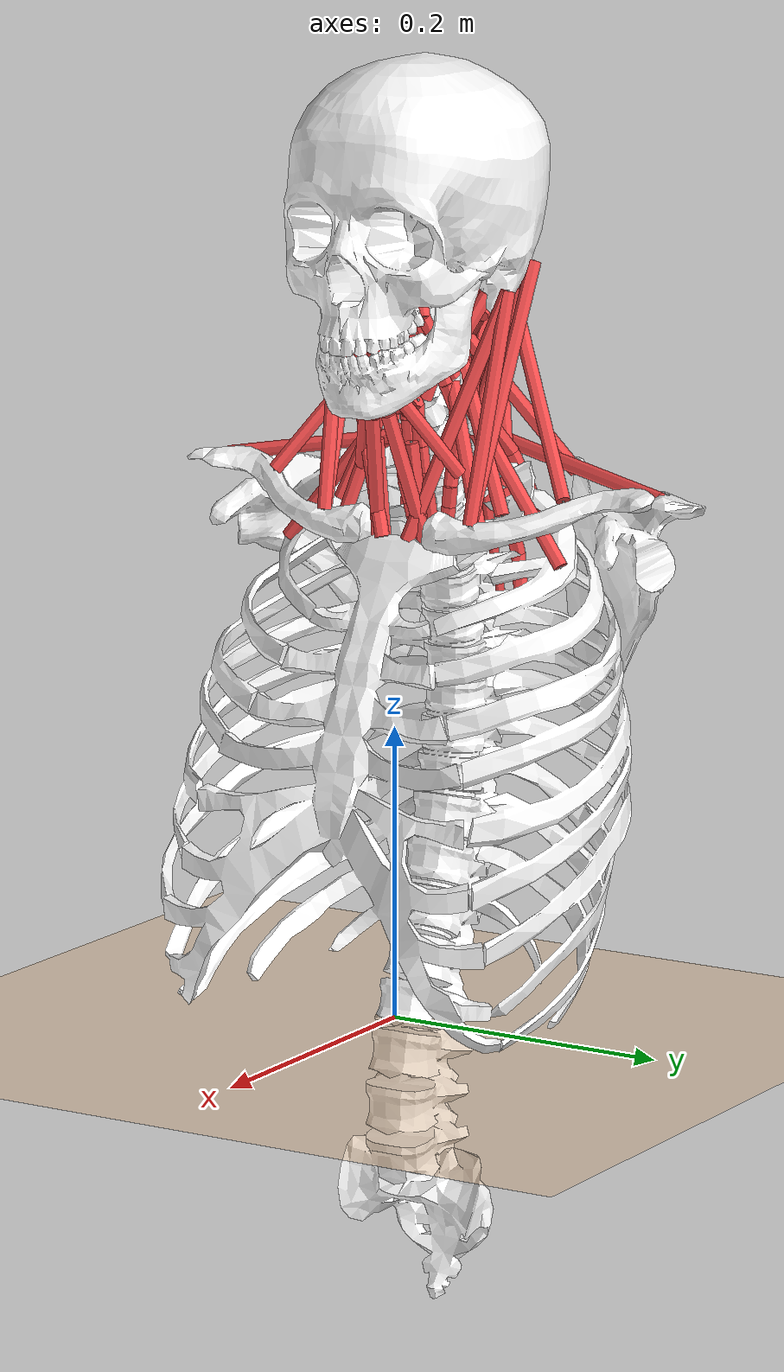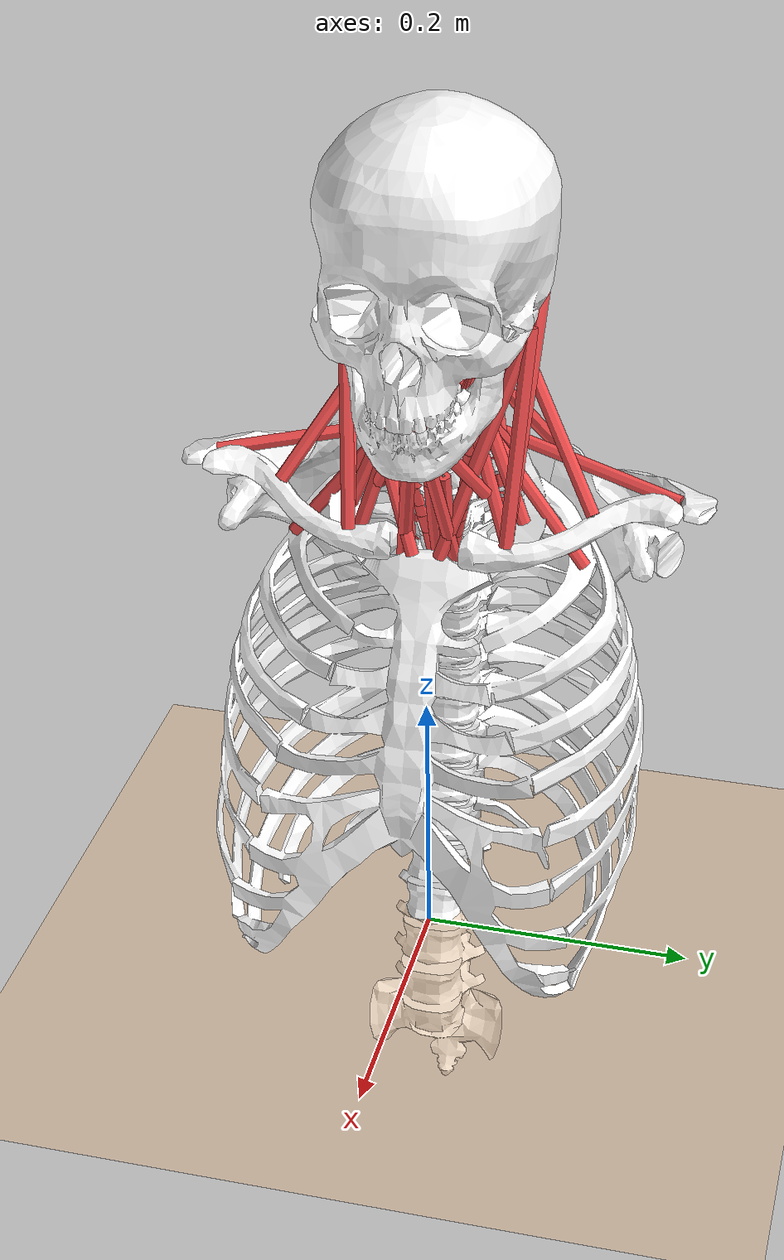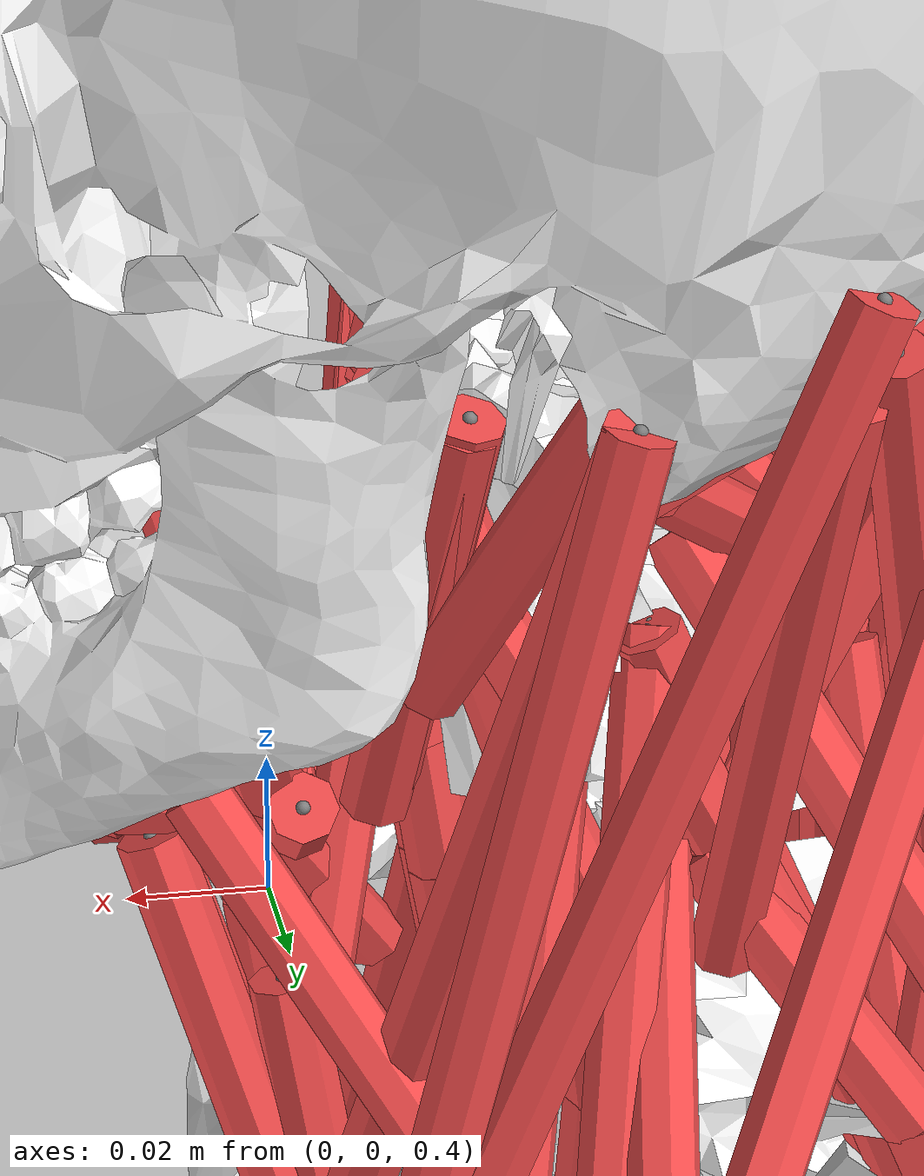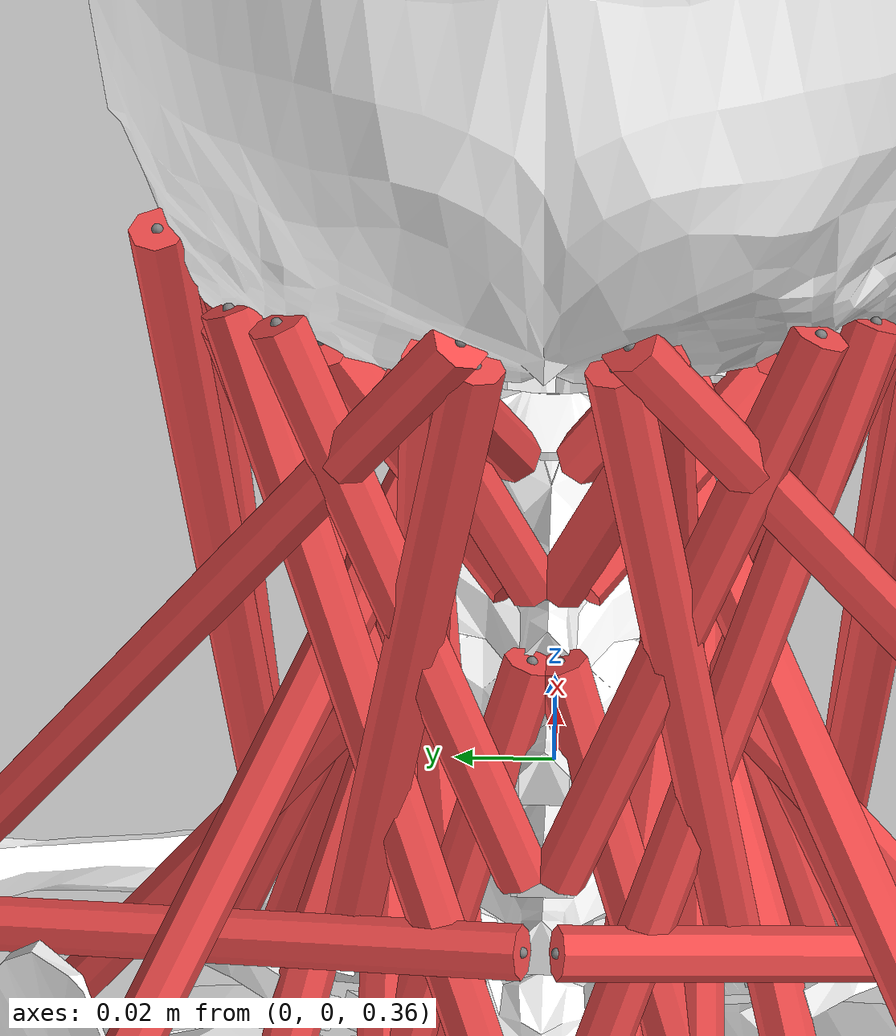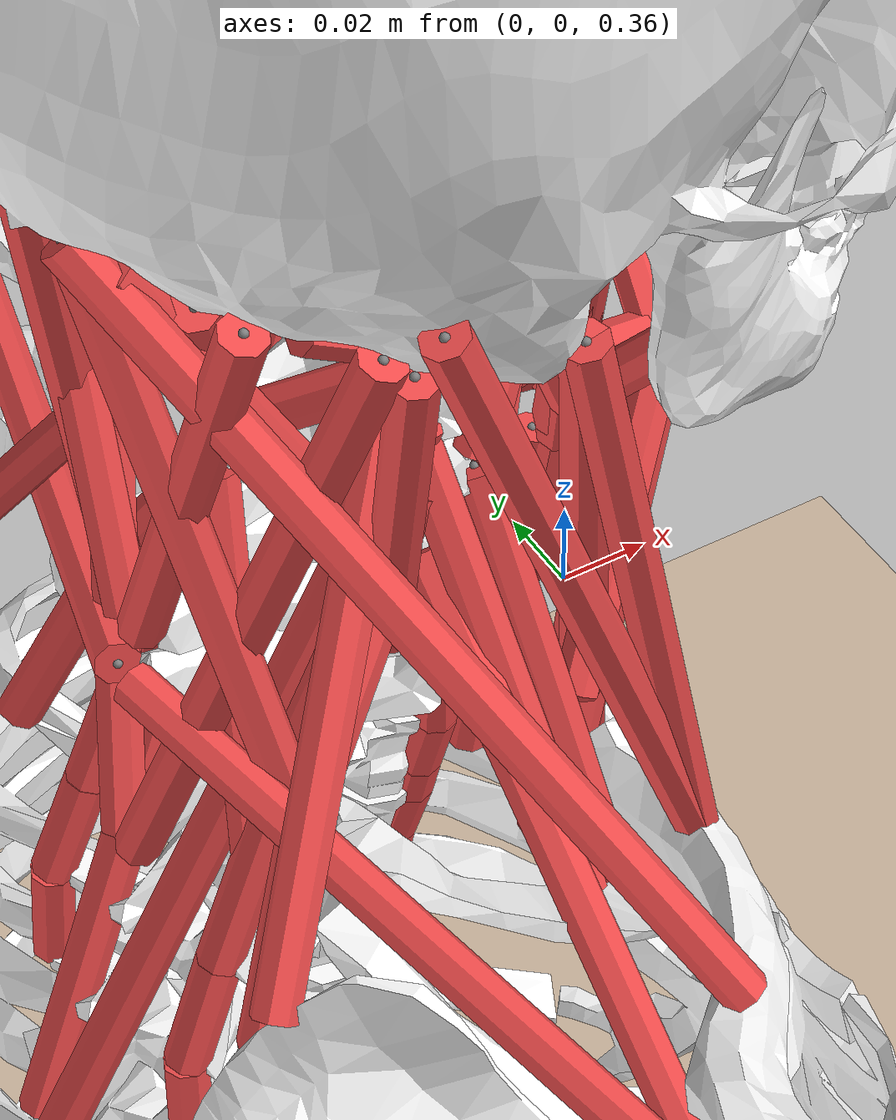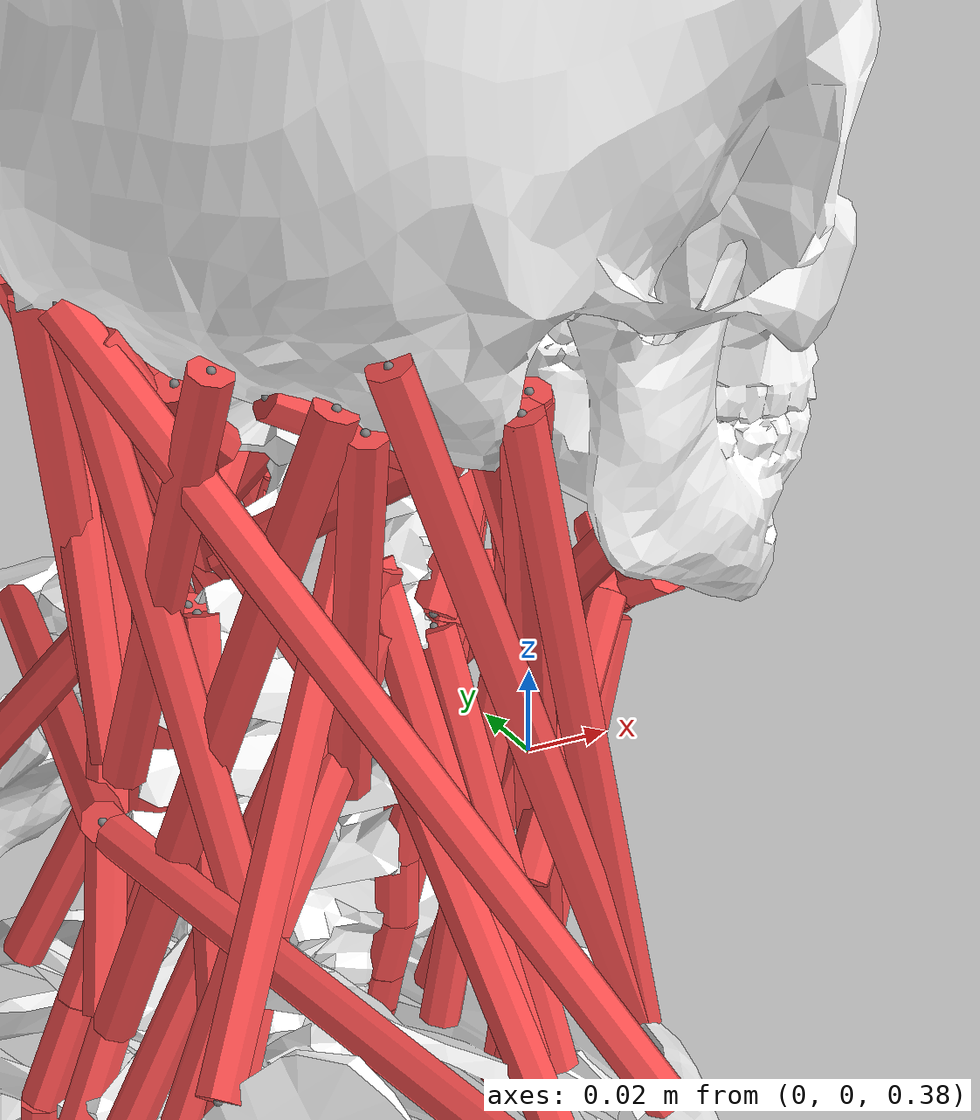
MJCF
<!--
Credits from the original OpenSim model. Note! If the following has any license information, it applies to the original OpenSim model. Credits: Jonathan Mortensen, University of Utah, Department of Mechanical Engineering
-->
<mujoco model="template">
  <!-- This model has been converted from an OpenSim model. Model conversion by MyoConverter https://github.com/MyoHub/myoconverter. This model is licensed under Apache 2.0. -->
  <!-- Note: inertiagrouprange="0 1" means that groups 0-1 will be used to infer masses/inertias, and groups 2-5 are
  only for visualisation (e.g. wrapping objects) !-->
  <compiler inertiafromgeom="auto" angle="radian" balanceinertia="true" boundmass="0.001" boundinertia="0.001" inertiagrouprange="0 1">
    <lengthrange inttotal="50" useexisting="true"/>
  </compiler>
  <option collision="predefined"/>
  <visual>
    <scale framelength="0.5" framewidth="0.01"/>
  </visual>
  <default>
    <joint limited="true" damping="0.05" armature="0.00001" stiffness="0"/>
    <geom rgba="0.8 0.6 .4 1" margin="0.001"/>
    <site size="0.001"/>
    <tendon width="0.005" rgba=".95 .3 .3 1" limited="false"/>
    <default class="muscle">
      <muscle ctrllimited="true" ctrlrange="0 1" scale="200"/>
    </default>
    <default class="motor">
      <general gainprm="5 0 0 0 0 0 0 0 0 0"/>
    </default>
  </default>
  <option timestep="0.002"/>
  <!-- nuser_jnt=1, the parameter is used to store default value of the joint, and nkey=1 to store keyframe with
   default joint positions set !-->
  <size njmax="1000" nconmax="400" nuser_jnt="1" nkey="1"/>
  <worldbody>
    <!-- The converter script assumes a body named 'ground' exists as a child element of worldbody -->
    <body name="ground" euler="1.571 0 0">
      <geom name="ground-plane" pos="0 0 0" euler="-1.571 0 0" size="10 10 0.125" type="plane" rgba="1.0 0.7 0.4 1.0" condim="3"/>
    </body>
    <light directional="true"/>
    <body name="spine" pos="0 0 0" euler="1.571 0 0">
      <inertial mass="70" pos="0 0 0" fullinertia="1 1 1 0 0 0"/>
      <geom name="spine_geom_1" type="mesh" mesh="spine_geom_1_tlspine" rgba="1 1 1 1" group="0"/>
      <joint name="spine_tx" range="-1 1" limited="true" user="-3.97872216927308e-17" ref="0" axis="1 0 0" type="slide" damping="0" stiffness="0"/>
      <joint name="spine_ty" range="-1 1" limited="true" user="8.44526185968539e-17" ref="0" axis="0 1 0" type="slide" damping="0" stiffness="0"/>
      <joint name="spine_tz" range="-1 1" limited="true" user="-7.30666612219483e-19" ref="0" axis="0 0 1" type="slide" damping="0" stiffness="0"/>
      <joint name="gndpitch" range="-3.142 3.142" limited="true" user="7.35301000738626e-11" ref="0" axis="0 0 1" type="hinge" damping="0" stiffness="0"/>
      <joint name="gndroll" range="-3.142 3.142" limited="true" user="1.39668511395652e-11" ref="0" axis="1 0 0" type="hinge" damping="0" stiffness="0"/>
      <joint name="gndyaw" range="-3.142 3.142" limited="true" user="7.7498968569503e-12" ref="0" axis="0 1 0" type="hinge" damping="0" stiffness="0"/>
      <body name="rscapula" pos="-0.0366 0.3623 0.1837" euler="0.1745 -0.2967 -0.1745">
        <inertial mass="1" pos="0 0 0" fullinertia="1 1 0.5 0 0 0"/>
        <geom name="rscapula_geom_1" type="mesh" mesh="rscapula_geom_1_rscapula" rgba="1 1 1 1" group="0"/>
        <site name="trap_acr_trap_acr-P1" pos="-0.023789999999999999 -0.0091599999999999997 -0.0073600000000000002"/>
        <site name="levator_scap_levator_scap-P1" pos="-0.097489999999999993 -0.036240000000000001 -0.081460000000000005"/>
        <site name="RCAJ_marker" group="4" pos="0 0.01 0.02" rgba="1 0.1 0.5 0.5" size="0.01"/>
      </body>
      <body name="rclavicle" pos="-0.0118 0.3353 0.022" euler="0 0.1396 0">
        <inertial mass="1" pos="0 0 0" fullinertia="1 1 0.5 0 0 0"/>
        <geom name="rclavicle_geom_1" type="mesh" mesh="rclavicle_geom_1_rclavicle" rgba="1 1 1 1" group="0"/>
        <site name="cleid_mast_cleid_mast-P1" pos="0.0038800000000000002 0.0054200000000000003 0.035200000000000002"/>
        <site name="cleid_occ_cleid_occ-P1" pos="0.0038800000000000002 0.0054200000000000003 0.035200000000000002"/>
        <site name="trap_cl_trap_cl-P1" pos="-0.029399999999999999 0.023199999999999998 0.086900000000000005"/>
      </body>
      <body name="lscapula" pos="-0.0366 0.3623 -0.1837" euler="-0.1745 0.2967 -0.1745">
        <inertial mass="1" pos="0 0 0" fullinertia="1 1 0.5 0 0 0"/>
        <geom name="lscapula_geom_1" type="mesh" mesh="lscapula_geom_1_lscapula" rgba="1 1 1 1" group="0"/>
        <site name="trap_acr_L_trap_acr_L-P1" pos="-0.023789999999999999 -0.0091599999999999997 0.0073600000000000002"/>
        <site name="levator_scap_L_levator_scap_L-P1" pos="-0.097489999999999993 -0.036240000000000001 0.081460000000000005"/>
        <site name="LCAJ_marker" group="4" pos="0 0.01 -0.02" rgba="1 0.1 0.5 0.5" size="0.01"/>
      </body>
      <body name="lclavicle" pos="-0.0118 0.3353 -0.022" euler="0 -0.1396 0">
        <inertial mass="1" pos="0 0 0" fullinertia="1 1 0.5 0 0 0"/>
        <geom name="lclavicle_geom_1" type="mesh" mesh="lclavicle_geom_1_lclavicle" rgba="1 1 1 1" group="0"/>
        <site name="cleid_mast_L_cleid_mast_L-P1" pos="0.0038800000000000002 0.0054200000000000003 -0.035200000000000002"/>
        <site name="cleid_occ_L_cleid_occ_L-P1" pos="0.0038800000000000002 0.0054200000000000003 -0.035200000000000002"/>
        <site name="trap_cl_L_trap_cl_L-P1" pos="-0.029399999999999999 0.023199999999999998 -0.086900000000000005"/>
      </body>
      <body name="ribcage" pos="0 0 0" euler="0 0 0">
        <inertial mass="1" pos="0 0 0" fullinertia="1 1 0.75 0 0 0"/>
        <geom name="ribcage_geom_1" type="mesh" mesh="ribcage_geom_1_ribcage" rgba="1 1 1 1" group="0"/>
        <site name="Sterno_hyoid_default" pos="-0.014033 0.31252000000000002 0.01984"/>
        <site name="SternoThyroid_default" pos="-0.014643 0.30575000000000002 0.015299999999999999"/>
        <site name="Omo_hyoid_default" pos="-0.021033 0.37082999999999999 0.037740000000000003"/>
        <site name="Sterno_hyoid_L_default" pos="-0.014033 0.31252000000000002 -0.01984"/>
        <site name="SternoThyroid_L_default" pos="-0.014643 0.30575000000000002 -0.015299999999999999"/>
        <site name="Omo_hyoid_L_default" pos="-0.021033 0.37082999999999999 -0.037740000000000003"/>
        <site name="stern_mast_stern_mast-P1" pos="-0.00069999999999999999 0.32690000000000002 0.0095999999999999992"/>
        <site name="stern_mast_L_stern_mast_L-P1" pos="-0.00069999999999999999 0.32690000000000002 -0.0095999999999999992"/>
        <site name="scalenus_ant_scalenus_ant-P1" pos="-0.021389999999999999 0.33245999999999998 0.052900000000000003"/>
        <site name="scalenus_ant_L_scalenus_ant_L-P1" pos="-0.021389999999999999 0.33245999999999998 -0.052900000000000003"/>
        <site name="scalenus_med_scalenus_med-P1" pos="-0.033980000000000003 0.34333000000000002 0.062700000000000006"/>
        <site name="scalenus_med_L_scalenus_med_L-P1" pos="-0.033980000000000003 0.34333000000000002 -0.062700000000000006"/>
        <site name="scalenus_post_scalenus_post-P1" pos="-0.036380000000000003 0.31269999999999998 0.1062"/>
        <site name="scalenus_post_L_scalenus_post_L-P1" pos="-0.036380000000000003 0.31269999999999998 -0.1062"/>
        <site name="SJN_marker" group="4" pos="0.02 0.3516 0" rgba="1 0.1 0.5 0.5" size="0.01"/>
      </body>
      <body name="cerv7" pos="-0.05434 0.367 0" euler="0 0 0">
        <inertial mass="0.58408467400069497" pos="-0.00020000000000000001 0.0071000000000000004 0" fullinertia="0.02 0.080000000000000002 0.02 0 0 0"/>
        <geom name="cerv7_geom_1" type="mesh" mesh="cerv7_geom_1_rotatedcerv7" rgba="1 1 1 1" group="0"/>
        <joint name="pitch2" range="-0.05702 0.08294" limited="true" user="1.1800349671610618e-07" ref="0" axis="0 0 1" type="hinge"/>
        <joint name="roll2" range="-0.04492 0.04492" limited="true" user="5.28570985844188e-18" ref="0" axis="1 0 0" type="hinge"/>
        <joint name="yaw2" range="-0.02969 0.02969" limited="true" user="1.3160007532593355e-17" ref="0" axis="0 1 0" type="hinge"/>
        <body name="cerv6" pos="0.003837 0.01645 0" euler="0 0 0">
          <inertial mass="0.50774885522040603" pos="0.00020000000000000001 0.0064000000000000003 0" fullinertia="0.02 0.080000000000000002 0.02 0 0 0"/>
          <geom name="cerv6_geom_1" type="mesh" mesh="cerv6_geom_1_cerv6" rgba="1 1 1 1" group="0"/>
          <joint name="aux7jnt_r3" range="-1.57 1.57" limited="false" user="2.22895266139609e-07" ref="0" axis="0 0 1" type="hinge"/>
          <joint name="aux7jnt_r1" range="-1.57 1.57" limited="false" user="0.0" ref="0" axis="1 0 0" type="hinge"/>
          <joint name="aux7jnt_r2" range="-1.57 1.57" limited="false" user="0.0" ref="0" axis="0 1 0" type="hinge"/>
          <body name="cerv5" pos="0.00418 0.0179 0" euler="0 0 0">
            <inertial mass="0.42909999999999998" pos="0.0001 0.0063 0" fullinertia="0.02 0.080000000000000002 0.02 0 0 0"/>
            <geom name="cerv5_geom_1" type="mesh" mesh="cerv5_geom_1_cerv5" rgba="1 1 1 1" group="0"/>
            <joint name="aux6jnt_r3" range="-1.57 1.57" limited="false" user="2.62229082107135e-07" ref="0" axis="0 0 1" type="hinge"/>
            <joint name="aux6jnt_r1" range="-1.57 1.57" limited="false" user="0.0" ref="0" axis="1 0 0" type="hinge"/>
            <joint name="aux6jnt_r2" range="-1.57 1.57" limited="false" user="0.0" ref="0" axis="0 1 0" type="hinge"/>
            <body name="cerv4" pos="0.00341 0.01917 0" euler="0 0 0">
              <inertial mass="0.42331681300000001" pos="-0.00029999999999999997 0.0067000000000000002 0" fullinertia="0.02 0.080000000000000002 0.02 0 0 0"/>
              <geom name="cerv4_geom_1" type="mesh" mesh="cerv4_geom_1_cerv4" rgba="1 1 1 1" group="0"/>
              <joint name="aux5jnt_r3" range="-1.57 1.57" limited="false" user="2.62229082107135e-07" ref="0" axis="0 0 1" type="hinge"/>
              <joint name="aux5jnt_r1" range="-1.57 1.57" limited="false" user="0.0" ref="0" axis="1 0 0" type="hinge"/>
              <joint name="aux5jnt_r2" range="-1.57 1.57" limited="false" user="0.0" ref="0" axis="0 1 0" type="hinge"/>
              <body name="cerv3" pos="0.00261 0.0154 0" euler="0 0 0">
                <inertial mass="0.419847003" pos="-0.00080000000000000004 0.0071000000000000004 0" fullinertia="0.02 0.080000000000000002 0.02 0 0 0"/>
                <geom name="cerv3_geom_1" type="mesh" mesh="cerv3_geom_1_cerv3" rgba="1 1 1 1" group="0"/>
                <joint name="aux4jnt_r3" range="-1.57 1.57" limited="false" user="1.96671811580351e-07" ref="0" axis="0 0 1" type="hinge"/>
                <joint name="aux4jnt_r1" range="-1.57 1.57" limited="false" user="0.0" ref="0" axis="1 0 0" type="hinge"/>
                <joint name="aux4jnt_r2" range="-1.57 1.57" limited="false" user="0.0" ref="0" axis="0 1 0" type="hinge"/>
                <body name="cerv2" pos="-0.00018 0.01629 0" euler="0 0 0">
                  <inertial mass="0.58755448399999999" pos="-0.001 0.0058999999999999999 0" fullinertia="0.02 0.080000000000000002 0.02 0 0 0"/>
                  <geom name="cerv2_geom_1" type="mesh" mesh="cerv2_geom_1_cerv2" rgba="1 1 1 1" group="0"/>
                  <joint name="aux3jnt_r3" range="-1.57 1.57" limited="false" user="1.31114541053568e-07" ref="0" axis="0 0 1" type="hinge"/>
                  <joint name="aux3jnt_r1" range="-1.57 1.57" limited="false" user="0.0" ref="0" axis="1 0 0" type="hinge"/>
                  <joint name="aux3jnt_r2" range="-1.57 1.57" limited="false" user="0.0" ref="0" axis="0 1 0" type="hinge"/>
                  <body name="cerv1" pos="-0.03556 0.01776 0" euler="0 0 0">
                    <inertial mass="0.46726773900000002" pos="0.031199999999999999 0.0019 0" fullinertia="0.02 0.080000000000000002 0.02 0 0 0"/>
                    <geom name="cerv1_geom_1" type="mesh" mesh="cerv1_geom_1_cerv1" rgba="1 1 1 1" group="0"/>
                    <joint name="pitch1" range="-0.124 0.186" limited="true" user="6.98927181571122e-07" ref="0" axis="0 0 1" type="hinge"/>
                    <joint name="roll1" range="-0.05236 0.05236" limited="true" user="3.121760331510614e-17" ref="0" axis="1 0 0" type="hinge"/>
                    <joint name="yaw1" range="-0.5896 0.5896" limited="true" user="-3.6371023416760163e-17" ref="0" axis="0 1 0" type="hinge"/>
                    <body name="skull" pos="0.04335 0.01492 0" euler="0 0 0">
                      <inertial mass="4.2999999999999998" pos="0.017299999999999999 0.063 0" fullinertia="0.020729999999999998 0.014999999999999999 0.022605 0 0 0"/>
                      <geom name="skull_geom_1" type="mesh" mesh="skull_geom_1_skull" rgba="1 1 1 1" group="0"/>
                      <joint name="aux1jnt_r3" range="-1.57 1.57" limited="false" user="8.75233291594014e-07" ref="0" axis="0 0 1" type="hinge"/>
                      <joint name="aux1jnt_r1" range="-1.57 1.57" limited="false" user="0.0" ref="0" axis="1 0 0" type="hinge"/>
                      <joint name="aux1jnt_r2" range="-1.57 1.57" limited="false" user="0.0" ref="0" axis="0 1 0" type="hinge"/>
                      <body name="jaw" pos="0 0 0" euler="0 0 0">
                        <inertial mass="0" pos="0 0.050000000000000003 0"/>
                        <geom name="jaw_geom_1" type="mesh" mesh="jaw_geom_1_jaw" rgba="1 1 1 1" group="0"/>
                      </body>
                      <site name="digastric_post_digastricpost-P1" pos="-0.0061000000000000004 0.0033999999999999998 0.047699999999999999"/>
                      <site name="digastric_ant_digastricpost-P1" pos="0.030300000000000001 -0.064299999999999996 0.017299999999999999"/>
                      <site name="Geniohyoid_digastricpost-P2" pos="0.069099999999999995 -0.067299999999999999 0.0016000000000000001"/>
                      <site name="Mylohyoid_Post_digastricpost-P2" pos="0.041300000000000003 -0.038899999999999997 0.029100000000000001"/>
                      <site name="Mylohyoid_Ant_digastricpost-P2" pos="0.0579 -0.0596 0.015800000000000002"/>
                      <site name="Stylohyoid_Lat_digastricpost-P1" pos="0.011299999999999999 -0.00080000000000000004 0.037600000000000001"/>
                      <site name="Stylohyoid_Med_digastricpost-P1" pos="0.0118 -0.002 0.037600000000000001"/>
                      <site name="digastric_post_L_digastricpost-P1" pos="-0.0061000000000000004 0.0033999999999999998 -0.047699999999999999"/>
                      <site name="digastric_ant_L_digastricpost-P1" pos="0.030300000000000001 -0.064299999999999996 -0.017299999999999999"/>
                      <site name="Geniohyoid_L_digastricpost-P2" pos="0.069099999999999995 -0.067299999999999999 -0.0016000000000000001"/>
                      <site name="Mylohyoid_Post_L_digastricpost-P2" pos="0.041300000000000003 -0.038899999999999997 -0.029100000000000001"/>
                      <site name="Mylohyoid_Ant_L_digastricpost-P2" pos="0.0579 -0.0596 -0.015800000000000002"/>
                      <site name="Stylohyoid_Lat_L_digastricpost-P1" pos="0.011299999999999999 -0.00080000000000000004 -0.037600000000000001"/>
                      <site name="Stylohyoid_Med_L_digastricpost-P1" pos="0.0118 -0.002 -0.037600000000000001"/>
                      <site name="stern_mast_stern_mast-P2" pos="-0.0051000000000000004 0.0069300000000000004 0.064299999999999996"/>
                      <site name="stern_mast_L_stern_mast_L-P2" pos="-0.0051000000000000004 0.0069300000000000004 -0.064299999999999996"/>
                      <site name="cleid_mast_cleid_mast-P2" pos="-0.0051000000000000004 0.0069300000000000004 0.064299999999999996"/>
                      <site name="cleid_mast_L_cleid_mast_L-P2" pos="-0.0051000000000000004 0.0069300000000000004 -0.064299999999999996"/>
                      <site name="cleid_occ_cleid_occ-P2" pos="-0.035000000000000003 0.023 0.066400000000000001"/>
                      <site name="cleid_occ_L_cleid_occ_L-P2" pos="-0.035000000000000003 0.023 -0.066400000000000001"/>
                      <site name="long_cap_sklc4_long_cap_sklc4-P5" pos="0.0097999999999999997 0.015959999999999998 0.0035999999999999999"/>
                      <site name="long_cap_sklc4_L_long_cap_sklc4_L-P5" pos="0.0097999999999999997 0.015959999999999998 -0.0035999999999999999"/>
                      <site name="trap_cl_trap_cl-P2" pos="-0.080310000000000006 0.026040000000000001 0.01324"/>
                      <site name="trap_cl_L_trap_cl_L-P2" pos="-0.080310000000000006 0.026040000000000001 -0.01324"/>
                      <site name="splen_cap_sklc6_splen_cap_sklc6-P2" pos="-0.06164 0.019179999999999999 0.043999999999999997"/>
                      <site name="splen_cap_sklc6_L_splen_cap_sklc6_L-P2" pos="-0.06164 0.019179999999999999 -0.043999999999999997"/>
                      <site name="splen_cap_sklthx_splen_cap_sklthx-P2" pos="-0.040160000000000001 0.010999999999999999 0.05423"/>
                      <site name="splen_cap_sklthx_L_splen_cap_sklthx_L-P2" pos="-0.040160000000000001 0.010999999999999999 -0.05423"/>
                      <site name="semi_cap_sklc5_semi_cap_sklc5-P2" pos="-0.074410000000000004 0.02 0.017999999999999999"/>
                      <site name="semi_cap_sklc5_L_semi_cap_sklc5_L-P2" pos="-0.074410000000000004 0.02 -0.017999999999999999"/>
                      <site name="semi_cap_sklthx_semi_cap_sklthx-P2" pos="-0.07671 0.02 0.0111"/>
                      <site name="semi_cap_sklthx_L_semi_cap_sklthx_L-P2" pos="-0.07671 0.02 -0.0111"/>
                      <site name="longissi_cap_sklc6_longissi_cap_sklc6-P2" pos="-0.0344 0.0051000000000000004 0.055"/>
                      <site name="longissi_cap_sklc6_L_longissi_cap_sklc6_L-P2" pos="-0.0344 0.0051000000000000004 -0.055"/>
                      <site name="rectcap_post_maj_rectcap_post_maj-P2" pos="-0.060400000000000002 0.0089999999999999993 0.023"/>
                      <site name="rectcap_post_maj_L_rectcap_post_maj_L-P2" pos="-0.060400000000000002 0.0089999999999999993 -0.023"/>
                      <site name="rectcap_post_min_rectcap_post_min-P2" pos="-0.066699999999999995 0.0089999999999999993 0.014500000000000001"/>
                      <site name="rectcap_post_min_L_rectcap_post_min_L-P2" pos="-0.066699999999999995 0.0089999999999999993 -0.014500000000000001"/>
                      <site name="obl_cap_sup_obl_cap_sup-P2" pos="-0.047579999999999997 0.0093100000000000006 0.038179999999999999"/>
                      <site name="obl_cap_sup_L_obl_cap_sup_L-P2" pos="-0.047579999999999997 0.0093100000000000006 -0.038179999999999999"/>
                      <site name="RAH_marker" group="4" pos="0.1 0.1 0.05" rgba="1 0.1 0.5 0.5" size="0.01"/>
                      <site name="LAH_marker" group="4" pos="0.1 0.1 -0.06" rgba="1 0.1 0.5 0.5" size="0.01"/>
                      <site name="RPH_marker" group="4" pos="-0.09 0.1 0.045" rgba="1 0.1 0.5 0.5" size="0.01"/>
                      <site name="LPH_marker" group="4" pos="-0.09 0.1 -0.045" rgba="1 0.1 0.5 0.5" size="0.01"/>
                    </body>
                    <site name="digastric_ant_digastricpost-P2" pos="0.072889999999999996 -0.057579999999999999 0.0057000000000000002"/>
                    <site name="Geniohyoid_digastricpost-P1" pos="0.071729799999999996 -0.053790600000000001 0.0050944299999999996"/>
                    <site name="Mylohyoid_Post_digastricpost-P1" pos="0.075249999999999997 -0.055879999999999999 0.0030999999999999999"/>
                    <site name="Mylohyoid_Ant_digastricpost-P1" pos="0.097250000000000003 -0.056680000000000001 -0.0030999999999999999"/>
                    <site name="Stylohyoid_Lat_digastricpost-P2" pos="0.064338099999999995 -0.049683199999999997 0.015440000000000001"/>
                    <site name="Stylohyoid_Med_digastricpost-P2" pos="0.063266100000000006 -0.045053799999999998 0.016252099999999998"/>
                    <site name="digastric_ant_L_digastricpost-P2" pos="0.072889999999999996 -0.057579999999999999 -0.0057000000000000002"/>
                    <site name="Geniohyoid_L_digastricpost-P1" pos="0.071494699999999994 -0.0538159 -0.0063031199999999997"/>
                    <site name="Mylohyoid_Post_L_digastricpost-P1" pos="0.075249999999999997 -0.055879999999999999 -0.0030999999999999999"/>
                    <site name="Mylohyoid_Ant_L_digastricpost-P1" pos="0.097250000000000003 -0.056680000000000001 0.0030999999999999999"/>
                    <site name="Stylohyoid_Lat_L_digastricpost-P2" pos="0.063682199999999994 -0.049753600000000002 -0.016353099999999999"/>
                    <site name="Stylohyoid_Med_L_digastricpost-P2" pos="0.062577199999999999 -0.0451277 -0.017140800000000001"/>
                    <site name="long_cap_sklc4_long_cap_sklc4-P4" pos="0.058180000000000003 0.0030899999999999999 0.01159"/>
                    <site name="long_cap_sklc4_L_long_cap_sklc4_L-P4" pos="0.058180000000000003 0.0030899999999999999 -0.01159"/>
                    <site name="long_col_c1thx_long_col_c1thx-P8" pos="0.058250000000000003 0.0048199999999999996 0.0030999999999999999"/>
                    <site name="long_col_c1thx_L_long_col_c1thx_L-P8" pos="0.058250000000000003 0.0048199999999999996 -0.0030999999999999999"/>
                    <site name="long_col_c1c5_long_col_c1c5-P4" pos="0.057250000000000002 0.0048199999999999996 0.0061999999999999998"/>
                    <site name="long_col_c1c5_L_long_col_c1c5_L-P4" pos="0.057250000000000002 0.0048199999999999996 -0.0061999999999999998"/>
                    <site name="rectcap_post_min_rectcap_post_min-P1" pos="6.9999999999999994e-05 0.00089999999999999998 0.0061000000000000004"/>
                    <site name="rectcap_post_min_L_rectcap_post_min_L-P1" pos="6.9999999999999994e-05 0.00089999999999999998 -0.0061000000000000004"/>
                    <site name="obl_cap_sup_obl_cap_sup-P1" pos="0.035049999999999998 0.0038500000000000001 0.042000000000000003"/>
                    <site name="obl_cap_sup_L_obl_cap_sup_L-P1" pos="0.035049999999999998 0.0038500000000000001 -0.042000000000000003"/>
                    <site name="obl_cap_inf_obl_cap_inf-P2" pos="0.029960000000000001 0.00349 0.037909999999999999"/>
                    <site name="obl_cap_inf_L_obl_cap_inf_L-P2" pos="0.029960000000000001 0.00349 -0.037909999999999999"/>
                  </body>
                  <site name="long_cap_sklc4_long_cap_sklc4-P3" pos="0.0172 0.0082900000000000005 0.01477"/>
                  <site name="long_cap_sklc4_L_long_cap_sklc4_L-P3" pos="0.0172 0.0082900000000000005 -0.01477"/>
                  <site name="long_col_c1thx_long_col_c1thx-P7" pos="0.021219999999999999 0.0097300000000000008 0.0035599999999999998"/>
                  <site name="long_col_c1thx_L_long_col_c1thx_L-P7" pos="0.021219999999999999 0.0097300000000000008 -0.0035599999999999998"/>
                  <site name="long_col_c1c5_long_col_c1c5-P3" pos="0.017389999999999999 0.0015900000000000001 0.013650000000000001"/>
                  <site name="long_col_c1c5_L_long_col_c1c5_L-P3" pos="0.017389999999999999 0.0015900000000000001 -0.013650000000000001"/>
                  <site name="levator_scap_levator_scap-P2" pos="-0.011860000000000001 0.0072500000000000004 0.02121"/>
                  <site name="levator_scap_L_levator_scap_L-P2" pos="-0.011860000000000001 0.0072500000000000004 -0.02121"/>
                  <site name="rectcap_post_maj_rectcap_post_maj-P1" pos="-0.03637 -0.0064700000000000001 0.0023999999999999998"/>
                  <site name="rectcap_post_maj_L_rectcap_post_maj_L-P1" pos="-0.03637 -0.0064700000000000001 -0.0023999999999999998"/>
                  <site name="obl_cap_inf_obl_cap_inf-P1" pos="-0.03637 -0.0064700000000000001 0.00547"/>
                  <site name="obl_cap_inf_L_obl_cap_inf_L-P1" pos="-0.03637 -0.0064700000000000001 -0.00547"/>
                </body>
                <site name="digastric_post_digastricpost-P2" pos="0.023210000000000001 0.0059699999999999996 0.0287"/>
                <site name="Sterno_hyoid_stern_mast-P1" pos="0.057419999999999999 -0.023140000000000001 0.0062899999999999996"/>
                <site name="SternoThyroid_stern_mast-P1" pos="0.0404201 -0.043159999999999997 0.013299999999999999"/>
                <site name="Omo_hyoid_stern_mast-P1" pos="0.05212 -0.013899999999999999 0.0132"/>
                <site name="digastric_post_L_digastricpost-P2" pos="0.023210000000000001 0.0059699999999999996 -0.0287"/>
                <site name="Sterno_hyoid_L_stern_mast-P1" pos="0.057419999999999999 -0.023140000000000001 -0.0062899999999999996"/>
                <site name="SternoThyroid_L_stern_mast-P1" pos="0.0404201 -0.043159999999999997 -0.013299999999999999"/>
                <site name="Omo_hyoid_L_stern_mast-P1" pos="0.05212 -0.013899999999999999 -0.0132"/>
                <site name="scalenus_med_scalenus_med-P2" pos="-0.0090200000000000002 0.0098099999999999993 0.021190000000000001"/>
                <site name="scalenus_med_L_scalenus_med_L-P2" pos="-0.0090200000000000002 0.0098099999999999993 -0.021190000000000001"/>
                <site name="long_cap_sklc4_long_cap_sklc4-P2" pos="0.01197 0.01009 0.018970000000000001"/>
                <site name="long_cap_sklc4_L_long_cap_sklc4_L-P2" pos="0.01197 0.01009 -0.018970000000000001"/>
                <site name="long_col_c1thx_long_col_c1thx-P6" pos="0.022120000000000001 0.0060299999999999998 0.0036800000000000001"/>
                <site name="long_col_c1thx_L_long_col_c1thx_L-P6" pos="0.022120000000000001 0.0060299999999999998 -0.0036800000000000001"/>
                <site name="splen_cerv_c3thx_splen_cerv_c3thx-P2" pos="-0.0078700000000000003 0.01005 0.023650000000000001"/>
                <site name="splen_cerv_c3thx_L_splen_cerv_c3thx_L-P2" pos="-0.0078700000000000003 0.01005 -0.023650000000000001"/>
                <site name="semi_cerv_c3thx_semi_cerv_c3thx-P2" pos="-0.040640000000000003 -0.0032200000000000002 0.0023999999999999998"/>
                <site name="semi_cerv_c3thx_L_semi_cerv_c3thx_L-P2" pos="-0.040640000000000003 -0.0032200000000000002 -0.0023999999999999998"/>
              </body>
              <site name="scalenus_ant_scalenus_ant-P2" pos="0.0071300000000000001 0.0079000000000000008 0.023230000000000001"/>
              <site name="scalenus_ant_L_scalenus_ant_L-P2" pos="0.0071300000000000001 0.0079000000000000008 -0.023230000000000001"/>
              <site name="long_cap_sklc4_long_cap_sklc4-P1" pos="0.0065199999999999998 0.011639999999999999 0.024199999999999999"/>
              <site name="long_cap_sklc4_L_long_cap_sklc4_L-P1" pos="0.0065199999999999998 0.011639999999999999 -0.024199999999999999"/>
              <site name="long_col_c1thx_long_col_c1thx-P5" pos="0.02205 0.00331 0.00379"/>
              <site name="long_col_c1thx_L_long_col_c1thx_L-P5" pos="0.02205 0.00331 -0.00379"/>
              <site name="long_col_c1c5_long_col_c1c5-P2" pos="0.011209999999999999 0.0074900000000000001 0.0207"/>
              <site name="long_col_c1c5_L_long_col_c1c5_L-P2" pos="0.011209999999999999 0.0074900000000000001 -0.0207"/>
              <site name="longissi_cerv_c4thx_longissi_cerv_c4thx-P5" pos="-0.0070899999999999999 0.01157 0.026100000000000002"/>
              <site name="longissi_cerv_c4thx_L_longissi_cerv_c4thx_L-P5" pos="-0.0070899999999999999 0.01157 -0.026100000000000002"/>
            </body>
            <site name="scalenus_post_scalenus_post-P2" pos="-0.0032000000000000002 0.01371 0.025700000000000001"/>
            <site name="scalenus_post_L_scalenus_post_L-P2" pos="-0.0032000000000000002 0.01371 -0.025700000000000001"/>
            <site name="long_col_c1thx_long_col_c1thx-P4" pos="0.022280000000000001 0.0022799999999999999 0.0038999999999999998"/>
            <site name="long_col_c1thx_L_long_col_c1thx_L-P4" pos="0.022280000000000001 0.0022799999999999999 -0.0038999999999999998"/>
            <site name="long_col_c1c5_long_col_c1c5-P1" pos="0.0066899999999999998 0.0088900000000000003 0.023800000000000002"/>
            <site name="long_col_c1c5_L_long_col_c1c5_L-P1" pos="0.0066899999999999998 0.0088900000000000003 -0.023800000000000002"/>
            <site name="long_col_c5thx_long_col_c5thx-P8" pos="0.0066899999999999998 0.0088900000000000003 0.023800000000000002"/>
            <site name="long_col_c5thx_L_long_col_c5thx_L-P8" pos="0.0066899999999999998 0.0088900000000000003 -0.023800000000000002"/>
            <site name="semi_cap_sklc5_semi_cap_sklc5-P1" pos="-0.0093100000000000006 0.01154 0.0235"/>
            <site name="semi_cap_sklc5_L_semi_cap_sklc5_L-P1" pos="-0.0093100000000000006 0.01154 -0.0235"/>
            <site name="iliocost_cerv_c5rib_iliocost_cerv_c5rib-P3" pos="-0.0094000000000000004 0.012579999999999999 0.025999999999999999"/>
            <site name="iliocost_cerv_c5rib_L_iliocost_cerv_c5rib_L-P3" pos="-0.0094000000000000004 0.012579999999999999 -0.025999999999999999"/>
          </body>
          <site name="long_col_c1thx_long_col_c1thx-P3" pos="0.023140000000000001 0.00231 0.0040200000000000001"/>
          <site name="long_col_c1thx_L_long_col_c1thx_L-P3" pos="0.023140000000000001 0.00231 -0.0040200000000000001"/>
          <site name="long_col_c5thx_long_col_c5thx-P7" pos="0.0096100000000000005 0.0071300000000000001 0.022159999999999999"/>
          <site name="long_col_c5thx_L_long_col_c5thx_L-P7" pos="0.0096100000000000005 0.0071300000000000001 -0.022159999999999999"/>
          <site name="splen_cap_sklc6_splen_cap_sklc6-P1" pos="-0.048599999999999997 0.016469999999999999 0.0030500000000000002"/>
          <site name="splen_cap_sklc6_L_splen_cap_sklc6_L-P1" pos="-0.048599999999999997 0.016469999999999999 -0.0030500000000000002"/>
          <site name="longissi_cap_sklc6_longissi_cap_sklc6-P1" pos="-0.0081700000000000002 0.01515 0.02759"/>
          <site name="longissi_cap_sklc6_L_longissi_cap_sklc6_L-P1" pos="-0.0081700000000000002 0.01515 -0.02759"/>
        </body>
        <site name="long_col_c1thx_long_col_c1thx-P2" pos="0.023199999999999998 0.0011000000000000001 0.0040000000000000001"/>
        <site name="long_col_c1thx_L_long_col_c1thx_L-P2" pos="0.023199999999999998 0.0011000000000000001 -0.0040000000000000001"/>
        <site name="long_col_c5thx_long_col_c5thx-P6" pos="0.01111 0.0073099999999999997 0.019789999999999999"/>
        <site name="long_col_c5thx_L_long_col_c5thx_L-P6" pos="0.01111 0.0073099999999999997 -0.019789999999999999"/>
        <site name="trap_acr_trap_acr-P2" pos="-0.047699999999999999 0.019 0.0030500000000000002"/>
        <site name="trap_acr_L_trap_acr_L-P2" pos="-0.047699999999999999 0.019 -0.0030500000000000002"/>
      </body>
      <site name="long_col_c1thx_long_col_c1thx-P1" pos="-0.04888 0.30334 0.0037000000000000002"/>
      <site name="long_col_c1thx_L_long_col_c1thx_L-P1" pos="-0.04888 0.30334 -0.0037000000000000002"/>
      <site name="long_col_c5thx_long_col_c5thx-P1" pos="-0.04981 0.30296000000000001 0.0067999999999999996"/>
      <site name="long_col_c5thx_long_col_c5thx-P2" pos="-0.048250000000000001 0.32027 0.01022"/>
      <site name="long_col_c5thx_long_col_c5thx-P3" pos="-0.045659999999999999 0.33462999999999998 0.01337"/>
      <site name="long_col_c5thx_long_col_c5thx-P4" pos="-0.044659999999999998 0.34360000000000002 0.01508"/>
      <site name="long_col_c5thx_long_col_c5thx-P5" pos="-0.042389999999999997 0.35782999999999998 0.017780000000000001"/>
      <site name="long_col_c5thx_L_long_col_c5thx_L-P1" pos="-0.04981 0.30296000000000001 -0.0067999999999999996"/>
      <site name="long_col_c5thx_L_long_col_c5thx_L-P2" pos="-0.048250000000000001 0.32027 -0.01022"/>
      <site name="long_col_c5thx_L_long_col_c5thx_L-P3" pos="-0.045659999999999999 0.33462999999999998 -0.01337"/>
      <site name="long_col_c5thx_L_long_col_c5thx_L-P4" pos="-0.044659999999999998 0.34360000000000002 -0.01508"/>
      <site name="long_col_c5thx_L_long_col_c5thx_L-P5" pos="-0.042389999999999997 0.35782999999999998 -0.017780000000000001"/>
      <site name="splen_cap_sklthx_splen_cap_sklthx-P1" pos="-0.10384 0.33901999999999999 0.0030000000000000001"/>
      <site name="splen_cap_sklthx_L_splen_cap_sklthx_L-P1" pos="-0.10384 0.33901999999999999 -0.0030000000000000001"/>
      <site name="splen_cerv_c3thx_splen_cerv_c3thx-P1" pos="-0.12848000000000001 0.26222000000000001 0.0041000000000000003"/>
      <site name="splen_cerv_c3thx_L_splen_cerv_c3thx_L-P1" pos="-0.12848000000000001 0.26222000000000001 -0.0041000000000000003"/>
      <site name="semi_cap_sklthx_semi_cap_sklthx-P1" pos="-0.085389999999999994 0.37731999999999999 0.034700000000000002"/>
      <site name="semi_cap_sklthx_L_semi_cap_sklthx_L-P1" pos="-0.085389999999999994 0.37731999999999999 -0.034700000000000002"/>
      <site name="semi_cerv_c3thx_semi_cerv_c3thx-P1" pos="-0.088959999999999997 0.34997 0.026069999999999999"/>
      <site name="semi_cerv_c3thx_L_semi_cerv_c3thx_L-P1" pos="-0.088959999999999997 0.34997 -0.026069999999999999"/>
      <site name="longissi_cerv_c4thx_longissi_cerv_c4thx-P1" pos="-0.10994 0.27585999999999999 0.032149999999999998"/>
      <site name="longissi_cerv_c4thx_longissi_cerv_c4thx-P2" pos="-0.10918 0.30237999999999998 0.03041"/>
      <site name="longissi_cerv_c4thx_longissi_cerv_c4thx-P3" pos="-0.099779999999999994 0.32691999999999999 0.029190000000000001"/>
      <site name="longissi_cerv_c4thx_longissi_cerv_c4thx-P4" pos="-0.081299999999999997 0.373 0.027900000000000001"/>
      <site name="longissi_cerv_c4thx_L_longissi_cerv_c4thx_L-P1" pos="-0.10994 0.27585999999999999 -0.032149999999999998"/>
      <site name="longissi_cerv_c4thx_L_longissi_cerv_c4thx_L-P2" pos="-0.10918 0.30237999999999998 -0.03041"/>
      <site name="longissi_cerv_c4thx_L_longissi_cerv_c4thx_L-P3" pos="-0.099779999999999994 0.32691999999999999 -0.029190000000000001"/>
      <site name="longissi_cerv_c4thx_L_longissi_cerv_c4thx_L-P4" pos="-0.081299999999999997 0.373 -0.027900000000000001"/>
      <site name="iliocost_cerv_c5rib_iliocost_cerv_c5rib-P1" pos="-0.10349 0.32796999999999998 0.0533"/>
      <site name="iliocost_cerv_c5rib_iliocost_cerv_c5rib-P2" pos="-0.083739999999999995 0.37637999999999999 0.040349999999999997"/>
      <site name="iliocost_cerv_c5rib_L_iliocost_cerv_c5rib_L-P1" pos="-0.10349 0.32796999999999998 -0.0533"/>
      <site name="iliocost_cerv_c5rib_L_iliocost_cerv_c5rib_L-P2" pos="-0.083739999999999995 0.37637999999999999 -0.040349999999999997"/>
    </body>
  </worldbody>
  <asset>
    <texture type="skybox" builtin="gradient" rgb1="1 1 1" rgb2="0.6 0.8 1" width="256" height="256"/>
    <mesh name="spine_geom_1_tlspine" file="Geometry/tlspine.stl" scale="1 1 1"/>
    <mesh name="rscapula_geom_1_rscapula" file="Geometry/rscapula.stl" scale="1 1 1"/>
    <mesh name="rclavicle_geom_1_rclavicle" file="Geometry/rclavicle.stl" scale="1 1 1"/>
    <mesh name="lscapula_geom_1_lscapula" file="Geometry/lscapula.stl" scale="1 1 1"/>
    <mesh name="lclavicle_geom_1_lclavicle" file="Geometry/lclavicle.stl" scale="1 1 1"/>
    <mesh name="ribcage_geom_1_ribcage" file="Geometry/ribcage.stl" scale="1 1 1"/>
    <mesh name="cerv7_geom_1_rotatedcerv7" file="Geometry/rotatedcerv7.stl" scale="1 1 1"/>
    <mesh name="cerv6_geom_1_cerv6" file="Geometry/cerv6.stl" scale="1 1 1"/>
    <mesh name="cerv5_geom_1_cerv5" file="Geometry/cerv5.stl" scale="1 1 1"/>
    <mesh name="cerv4_geom_1_cerv4" file="Geometry/cerv4.stl" scale="1 1 1"/>
    <mesh name="cerv3_geom_1_cerv3" file="Geometry/cerv3.stl" scale="1 1 1"/>
    <mesh name="cerv2_geom_1_cerv2" file="Geometry/cerv2.stl" scale="1 1 1"/>
    <mesh name="cerv1_geom_1_cerv1" file="Geometry/cerv1.stl" scale="1 1 1"/>
    <mesh name="skull_geom_1_skull" file="Geometry/skull.stl" scale="1 1 1"/>
    <mesh name="jaw_geom_1_jaw" file="Geometry/jaw.stl" scale="1 1 1"/>
  </asset>
  <tendon>
    <!-- Leave this comment here to make 'tendon' element pretty printed !-->
    <spatial name="digastric_post_tendon">
      <site site="digastric_post_digastricpost-P1"/>
      <site site="digastric_post_digastricpost-P2"/>
    </spatial>
    <spatial name="digastric_ant_tendon">
      <site site="digastric_ant_digastricpost-P1"/>
      <site site="digastric_ant_digastricpost-P2"/>
    </spatial>
    <spatial name="Geniohyoid_tendon">
      <site site="Geniohyoid_digastricpost-P1"/>
      <site site="Geniohyoid_digastricpost-P2"/>
    </spatial>
    <spatial name="Mylohyoid_Post_tendon">
      <site site="Mylohyoid_Post_digastricpost-P1"/>
      <site site="Mylohyoid_Post_digastricpost-P2"/>
    </spatial>
    <spatial name="Mylohyoid_Ant_tendon">
      <site site="Mylohyoid_Ant_digastricpost-P1"/>
      <site site="Mylohyoid_Ant_digastricpost-P2"/>
    </spatial>
    <spatial name="Stylohyoid_Lat_tendon">
      <site site="Stylohyoid_Lat_digastricpost-P1"/>
      <site site="Stylohyoid_Lat_digastricpost-P2"/>
    </spatial>
    <spatial name="Stylohyoid_Med_tendon">
      <site site="Stylohyoid_Med_digastricpost-P1"/>
      <site site="Stylohyoid_Med_digastricpost-P2"/>
    </spatial>
    <spatial name="Sterno_hyoid_tendon">
      <site site="Sterno_hyoid_stern_mast-P1"/>
      <site site="Sterno_hyoid_default"/>
    </spatial>
    <spatial name="SternoThyroid_tendon">
      <site site="SternoThyroid_stern_mast-P1"/>
      <site site="SternoThyroid_default"/>
    </spatial>
    <spatial name="Omo_hyoid_tendon">
      <site site="Omo_hyoid_stern_mast-P1"/>
      <site site="Omo_hyoid_default"/>
    </spatial>
    <spatial name="digastric_post_L_tendon">
      <site site="digastric_post_L_digastricpost-P1"/>
      <site site="digastric_post_L_digastricpost-P2"/>
    </spatial>
    <spatial name="digastric_ant_L_tendon">
      <site site="digastric_ant_L_digastricpost-P1"/>
      <site site="digastric_ant_L_digastricpost-P2"/>
    </spatial>
    <spatial name="Geniohyoid_L_tendon">
      <site site="Geniohyoid_L_digastricpost-P1"/>
      <site site="Geniohyoid_L_digastricpost-P2"/>
    </spatial>
    <spatial name="Mylohyoid_Post_L_tendon">
      <site site="Mylohyoid_Post_L_digastricpost-P1"/>
      <site site="Mylohyoid_Post_L_digastricpost-P2"/>
    </spatial>
    <spatial name="Mylohyoid_Ant_L_tendon">
      <site site="Mylohyoid_Ant_L_digastricpost-P1"/>
      <site site="Mylohyoid_Ant_L_digastricpost-P2"/>
    </spatial>
    <spatial name="Stylohyoid_Lat_L_tendon">
      <site site="Stylohyoid_Lat_L_digastricpost-P1"/>
      <site site="Stylohyoid_Lat_L_digastricpost-P2"/>
    </spatial>
    <spatial name="Stylohyoid_Med_L_tendon">
      <site site="Stylohyoid_Med_L_digastricpost-P1"/>
      <site site="Stylohyoid_Med_L_digastricpost-P2"/>
    </spatial>
    <spatial name="Sterno_hyoid_L_tendon">
      <site site="Sterno_hyoid_L_stern_mast-P1"/>
      <site site="Sterno_hyoid_L_default"/>
    </spatial>
    <spatial name="SternoThyroid_L_tendon">
      <site site="SternoThyroid_L_stern_mast-P1"/>
      <site site="SternoThyroid_L_default"/>
    </spatial>
    <spatial name="Omo_hyoid_L_tendon">
      <site site="Omo_hyoid_L_stern_mast-P1"/>
      <site site="Omo_hyoid_L_default"/>
    </spatial>
    <spatial name="stern_mast_tendon">
      <site site="stern_mast_stern_mast-P1"/>
      <site site="stern_mast_stern_mast-P2"/>
    </spatial>
    <spatial name="stern_mast_L_tendon">
      <site site="stern_mast_L_stern_mast_L-P1"/>
      <site site="stern_mast_L_stern_mast_L-P2"/>
    </spatial>
    <spatial name="cleid_mast_tendon">
      <site site="cleid_mast_cleid_mast-P1"/>
      <site site="cleid_mast_cleid_mast-P2"/>
    </spatial>
    <spatial name="cleid_mast_L_tendon">
      <site site="cleid_mast_L_cleid_mast_L-P1"/>
      <site site="cleid_mast_L_cleid_mast_L-P2"/>
    </spatial>
    <spatial name="cleid_occ_tendon">
      <site site="cleid_occ_cleid_occ-P1"/>
      <site site="cleid_occ_cleid_occ-P2"/>
    </spatial>
    <spatial name="cleid_occ_L_tendon">
      <site site="cleid_occ_L_cleid_occ_L-P1"/>
      <site site="cleid_occ_L_cleid_occ_L-P2"/>
    </spatial>
    <spatial name="scalenus_ant_tendon">
      <site site="scalenus_ant_scalenus_ant-P1"/>
      <site site="scalenus_ant_scalenus_ant-P2"/>
    </spatial>
    <spatial name="scalenus_ant_L_tendon">
      <site site="scalenus_ant_L_scalenus_ant_L-P1"/>
      <site site="scalenus_ant_L_scalenus_ant_L-P2"/>
    </spatial>
    <spatial name="scalenus_med_tendon">
      <site site="scalenus_med_scalenus_med-P1"/>
      <site site="scalenus_med_scalenus_med-P2"/>
    </spatial>
    <spatial name="scalenus_med_L_tendon">
      <site site="scalenus_med_L_scalenus_med_L-P1"/>
      <site site="scalenus_med_L_scalenus_med_L-P2"/>
    </spatial>
    <spatial name="scalenus_post_tendon">
      <site site="scalenus_post_scalenus_post-P1"/>
      <site site="scalenus_post_scalenus_post-P2"/>
    </spatial>
    <spatial name="scalenus_post_L_tendon">
      <site site="scalenus_post_L_scalenus_post_L-P1"/>
      <site site="scalenus_post_L_scalenus_post_L-P2"/>
    </spatial>
    <spatial name="long_cap_sklc4_tendon">
      <site site="long_cap_sklc4_long_cap_sklc4-P1"/>
      <site site="long_cap_sklc4_long_cap_sklc4-P2"/>
      <site site="long_cap_sklc4_long_cap_sklc4-P3"/>
      <site site="long_cap_sklc4_long_cap_sklc4-P4"/>
      <site site="long_cap_sklc4_long_cap_sklc4-P5"/>
    </spatial>
    <spatial name="long_cap_sklc4_L_tendon">
      <site site="long_cap_sklc4_L_long_cap_sklc4_L-P1"/>
      <site site="long_cap_sklc4_L_long_cap_sklc4_L-P2"/>
      <site site="long_cap_sklc4_L_long_cap_sklc4_L-P3"/>
      <site site="long_cap_sklc4_L_long_cap_sklc4_L-P4"/>
      <site site="long_cap_sklc4_L_long_cap_sklc4_L-P5"/>
    </spatial>
    <spatial name="long_col_c1thx_tendon">
      <site site="long_col_c1thx_long_col_c1thx-P1"/>
      <site site="long_col_c1thx_long_col_c1thx-P2"/>
      <site site="long_col_c1thx_long_col_c1thx-P3"/>
      <site site="long_col_c1thx_long_col_c1thx-P4"/>
      <site site="long_col_c1thx_long_col_c1thx-P5"/>
      <site site="long_col_c1thx_long_col_c1thx-P6"/>
      <site site="long_col_c1thx_long_col_c1thx-P7"/>
      <site site="long_col_c1thx_long_col_c1thx-P8"/>
    </spatial>
    <spatial name="long_col_c1thx_L_tendon">
      <site site="long_col_c1thx_L_long_col_c1thx_L-P1"/>
      <site site="long_col_c1thx_L_long_col_c1thx_L-P2"/>
      <site site="long_col_c1thx_L_long_col_c1thx_L-P3"/>
      <site site="long_col_c1thx_L_long_col_c1thx_L-P4"/>
      <site site="long_col_c1thx_L_long_col_c1thx_L-P5"/>
      <site site="long_col_c1thx_L_long_col_c1thx_L-P6"/>
      <site site="long_col_c1thx_L_long_col_c1thx_L-P7"/>
      <site site="long_col_c1thx_L_long_col_c1thx_L-P8"/>
    </spatial>
    <spatial name="long_col_c1c5_tendon">
      <site site="long_col_c1c5_long_col_c1c5-P1"/>
      <site site="long_col_c1c5_long_col_c1c5-P2"/>
      <site site="long_col_c1c5_long_col_c1c5-P3"/>
      <site site="long_col_c1c5_long_col_c1c5-P4"/>
    </spatial>
    <spatial name="long_col_c1c5_L_tendon">
      <site site="long_col_c1c5_L_long_col_c1c5_L-P1"/>
      <site site="long_col_c1c5_L_long_col_c1c5_L-P2"/>
      <site site="long_col_c1c5_L_long_col_c1c5_L-P3"/>
      <site site="long_col_c1c5_L_long_col_c1c5_L-P4"/>
    </spatial>
    <spatial name="long_col_c5thx_tendon">
      <site site="long_col_c5thx_long_col_c5thx-P1"/>
      <site site="long_col_c5thx_long_col_c5thx-P2"/>
      <site site="long_col_c5thx_long_col_c5thx-P3"/>
      <site site="long_col_c5thx_long_col_c5thx-P4"/>
      <site site="long_col_c5thx_long_col_c5thx-P5"/>
      <site site="long_col_c5thx_long_col_c5thx-P6"/>
      <site site="long_col_c5thx_long_col_c5thx-P7"/>
      <site site="long_col_c5thx_long_col_c5thx-P8"/>
    </spatial>
    <spatial name="long_col_c5thx_L_tendon">
      <site site="long_col_c5thx_L_long_col_c5thx_L-P1"/>
      <site site="long_col_c5thx_L_long_col_c5thx_L-P2"/>
      <site site="long_col_c5thx_L_long_col_c5thx_L-P3"/>
      <site site="long_col_c5thx_L_long_col_c5thx_L-P4"/>
      <site site="long_col_c5thx_L_long_col_c5thx_L-P5"/>
      <site site="long_col_c5thx_L_long_col_c5thx_L-P6"/>
      <site site="long_col_c5thx_L_long_col_c5thx_L-P7"/>
      <site site="long_col_c5thx_L_long_col_c5thx_L-P8"/>
    </spatial>
    <spatial name="trap_cl_tendon">
      <site site="trap_cl_trap_cl-P1"/>
      <site site="trap_cl_trap_cl-P2"/>
    </spatial>
    <spatial name="trap_cl_L_tendon">
      <site site="trap_cl_L_trap_cl_L-P1"/>
      <site site="trap_cl_L_trap_cl_L-P2"/>
    </spatial>
    <spatial name="trap_acr_tendon">
      <site site="trap_acr_trap_acr-P1"/>
      <site site="trap_acr_trap_acr-P2"/>
    </spatial>
    <spatial name="trap_acr_L_tendon">
      <site site="trap_acr_L_trap_acr_L-P1"/>
      <site site="trap_acr_L_trap_acr_L-P2"/>
    </spatial>
    <spatial name="splen_cap_sklc6_tendon">
      <site site="splen_cap_sklc6_splen_cap_sklc6-P1"/>
      <site site="splen_cap_sklc6_splen_cap_sklc6-P2"/>
    </spatial>
    <spatial name="splen_cap_sklc6_L_tendon">
      <site site="splen_cap_sklc6_L_splen_cap_sklc6_L-P1"/>
      <site site="splen_cap_sklc6_L_splen_cap_sklc6_L-P2"/>
    </spatial>
    <spatial name="splen_cap_sklthx_tendon">
      <site site="splen_cap_sklthx_splen_cap_sklthx-P1"/>
      <site site="splen_cap_sklthx_splen_cap_sklthx-P2"/>
    </spatial>
    <spatial name="splen_cap_sklthx_L_tendon">
      <site site="splen_cap_sklthx_L_splen_cap_sklthx_L-P1"/>
      <site site="splen_cap_sklthx_L_splen_cap_sklthx_L-P2"/>
    </spatial>
    <spatial name="splen_cerv_c3thx_tendon">
      <site site="splen_cerv_c3thx_splen_cerv_c3thx-P1"/>
      <site site="splen_cerv_c3thx_splen_cerv_c3thx-P2"/>
    </spatial>
    <spatial name="splen_cerv_c3thx_L_tendon">
      <site site="splen_cerv_c3thx_L_splen_cerv_c3thx_L-P1"/>
      <site site="splen_cerv_c3thx_L_splen_cerv_c3thx_L-P2"/>
    </spatial>
    <spatial name="semi_cap_sklc5_tendon">
      <site site="semi_cap_sklc5_semi_cap_sklc5-P1"/>
      <site site="semi_cap_sklc5_semi_cap_sklc5-P2"/>
    </spatial>
    <spatial name="semi_cap_sklc5_L_tendon">
      <site site="semi_cap_sklc5_L_semi_cap_sklc5_L-P1"/>
      <site site="semi_cap_sklc5_L_semi_cap_sklc5_L-P2"/>
    </spatial>
    <spatial name="semi_cap_sklthx_tendon">
      <site site="semi_cap_sklthx_semi_cap_sklthx-P1"/>
      <site site="semi_cap_sklthx_semi_cap_sklthx-P2"/>
    </spatial>
    <spatial name="semi_cap_sklthx_L_tendon">
      <site site="semi_cap_sklthx_L_semi_cap_sklthx_L-P1"/>
      <site site="semi_cap_sklthx_L_semi_cap_sklthx_L-P2"/>
    </spatial>
    <spatial name="semi_cerv_c3thx_tendon">
      <site site="semi_cerv_c3thx_semi_cerv_c3thx-P1"/>
      <site site="semi_cerv_c3thx_semi_cerv_c3thx-P2"/>
    </spatial>
    <spatial name="semi_cerv_c3thx_L_tendon">
      <site site="semi_cerv_c3thx_L_semi_cerv_c3thx_L-P1"/>
      <site site="semi_cerv_c3thx_L_semi_cerv_c3thx_L-P2"/>
    </spatial>
    <spatial name="levator_scap_tendon">
      <site site="levator_scap_levator_scap-P1"/>
      <site site="levator_scap_levator_scap-P2"/>
    </spatial>
    <spatial name="levator_scap_L_tendon">
      <site site="levator_scap_L_levator_scap_L-P1"/>
      <site site="levator_scap_L_levator_scap_L-P2"/>
    </spatial>
    <spatial name="longissi_cap_sklc6_tendon">
      <site site="longissi_cap_sklc6_longissi_cap_sklc6-P1"/>
      <site site="longissi_cap_sklc6_longissi_cap_sklc6-P2"/>
    </spatial>
    <spatial name="longissi_cap_sklc6_L_tendon">
      <site site="longissi_cap_sklc6_L_longissi_cap_sklc6_L-P1"/>
      <site site="longissi_cap_sklc6_L_longissi_cap_sklc6_L-P2"/>
    </spatial>
    <spatial name="longissi_cerv_c4thx_tendon">
      <site site="longissi_cerv_c4thx_longissi_cerv_c4thx-P1"/>
      <site site="longissi_cerv_c4thx_longissi_cerv_c4thx-P2"/>
      <site site="longissi_cerv_c4thx_longissi_cerv_c4thx-P3"/>
      <site site="longissi_cerv_c4thx_longissi_cerv_c4thx-P4"/>
      <site site="longissi_cerv_c4thx_longissi_cerv_c4thx-P5"/>
    </spatial>
    <spatial name="longissi_cerv_c4thx_L_tendon">
      <site site="longissi_cerv_c4thx_L_longissi_cerv_c4thx_L-P1"/>
      <site site="longissi_cerv_c4thx_L_longissi_cerv_c4thx_L-P2"/>
      <site site="longissi_cerv_c4thx_L_longissi_cerv_c4thx_L-P3"/>
      <site site="longissi_cerv_c4thx_L_longissi_cerv_c4thx_L-P4"/>
      <site site="longissi_cerv_c4thx_L_longissi_cerv_c4thx_L-P5"/>
    </spatial>
    <spatial name="iliocost_cerv_c5rib_tendon">
      <site site="iliocost_cerv_c5rib_iliocost_cerv_c5rib-P1"/>
      <site site="iliocost_cerv_c5rib_iliocost_cerv_c5rib-P2"/>
      <site site="iliocost_cerv_c5rib_iliocost_cerv_c5rib-P3"/>
    </spatial>
    <spatial name="iliocost_cerv_c5rib_L_tendon">
      <site site="iliocost_cerv_c5rib_L_iliocost_cerv_c5rib_L-P1"/>
      <site site="iliocost_cerv_c5rib_L_iliocost_cerv_c5rib_L-P2"/>
      <site site="iliocost_cerv_c5rib_L_iliocost_cerv_c5rib_L-P3"/>
    </spatial>
    <spatial name="rectcap_post_maj_tendon">
      <site site="rectcap_post_maj_rectcap_post_maj-P1"/>
      <site site="rectcap_post_maj_rectcap_post_maj-P2"/>
    </spatial>
    <spatial name="rectcap_post_maj_L_tendon">
      <site site="rectcap_post_maj_L_rectcap_post_maj_L-P1"/>
      <site site="rectcap_post_maj_L_rectcap_post_maj_L-P2"/>
    </spatial>
    <spatial name="rectcap_post_min_tendon">
      <site site="rectcap_post_min_rectcap_post_min-P1"/>
      <site site="rectcap_post_min_rectcap_post_min-P2"/>
    </spatial>
    <spatial name="rectcap_post_min_L_tendon">
      <site site="rectcap_post_min_L_rectcap_post_min_L-P1"/>
      <site site="rectcap_post_min_L_rectcap_post_min_L-P2"/>
    </spatial>
    <spatial name="obl_cap_sup_tendon">
      <site site="obl_cap_sup_obl_cap_sup-P1"/>
      <site site="obl_cap_sup_obl_cap_sup-P2"/>
    </spatial>
    <spatial name="obl_cap_sup_L_tendon">
      <site site="obl_cap_sup_L_obl_cap_sup_L-P1"/>
      <site site="obl_cap_sup_L_obl_cap_sup_L-P2"/>
    </spatial>
    <spatial name="obl_cap_inf_tendon">
      <site site="obl_cap_inf_obl_cap_inf-P1"/>
      <site site="obl_cap_inf_obl_cap_inf-P2"/>
    </spatial>
    <spatial name="obl_cap_inf_L_tendon">
      <site site="obl_cap_inf_L_obl_cap_inf_L-P1"/>
      <site site="obl_cap_inf_L_obl_cap_inf_L-P2"/>
    </spatial>
  </tendon>
  <actuator>
    <!-- Leave this comment here to make 'actuator' element pretty printed !-->
    <muscle name="digastric_post" lengthrange="0.01 1" force="109.62" tendon="digastric_post_tendon" class="muscle" timeconst="0.01 0.04"/>
    <muscle name="digastric_ant" lengthrange="0.01 1" force="109.62" tendon="digastric_ant_tendon" class="muscle" timeconst="0.01 0.04"/>
    <muscle name="Geniohyoid" lengthrange="0.01 1" force="91.665000000000006" tendon="Geniohyoid_tendon" class="muscle" timeconst="0.01 0.04"/>
    <muscle name="Mylohyoid_Post" lengthrange="0.01 1" force="50.085000000000001" tendon="Mylohyoid_Post_tendon" class="muscle" timeconst="0.01 0.04"/>
    <muscle name="Mylohyoid_Ant" lengthrange="0.01 1" force="150.255" tendon="Mylohyoid_Ant_tendon" class="muscle" timeconst="0.01 0.04"/>
    <muscle name="Stylohyoid_Lat" lengthrange="0.01 1" force="18.417857139999999" tendon="Stylohyoid_Lat_tendon" class="muscle" timeconst="0.01 0.04"/>
    <muscle name="Stylohyoid_Med" lengthrange="0.01 1" force="18.417857139999999" tendon="Stylohyoid_Med_tendon" class="muscle" timeconst="0.01 0.04"/>
    <muscle name="Sterno_hyoid" lengthrange="0.01 1" force="54.810000000000002" tendon="Sterno_hyoid_tendon" class="muscle" timeconst="0.01 0.04"/>
    <muscle name="SternoThyroid" lengthrange="0.01 1" force="61.424999999999997" tendon="SternoThyroid_tendon" class="muscle" timeconst="0.01 0.04"/>
    <muscle name="Omo_hyoid" lengthrange="0.01 1" force="70.875" tendon="Omo_hyoid_tendon" class="muscle" timeconst="0.01 0.04"/>
    <muscle name="digastric_post_L" lengthrange="0.01 1" force="109.62" tendon="digastric_post_L_tendon" class="muscle" timeconst="0.01 0.04"/>
    <muscle name="digastric_ant_L" lengthrange="0.01 1" force="109.62" tendon="digastric_ant_L_tendon" class="muscle" timeconst="0.01 0.04"/>
    <muscle name="Geniohyoid_L" lengthrange="0.01 1" force="91.665000000000006" tendon="Geniohyoid_L_tendon" class="muscle" timeconst="0.01 0.04"/>
    <muscle name="Mylohyoid_Post_L" lengthrange="0.01 1" force="50.085000000000001" tendon="Mylohyoid_Post_L_tendon" class="muscle" timeconst="0.01 0.04"/>
    <muscle name="Mylohyoid_Ant_L" lengthrange="0.01 1" force="150.255" tendon="Mylohyoid_Ant_L_tendon" class="muscle" timeconst="0.01 0.04"/>
    <muscle name="Stylohyoid_Lat_L" lengthrange="0.01 1" force="18.417857139999999" tendon="Stylohyoid_Lat_L_tendon" class="muscle" timeconst="0.01 0.04"/>
    <muscle name="Stylohyoid_Med_L" lengthrange="0.01 1" force="18.417857139999999" tendon="Stylohyoid_Med_L_tendon" class="muscle" timeconst="0.01 0.04"/>
    <muscle name="Sterno_hyoid_L" lengthrange="0.01 1" force="54.810000000000002" tendon="Sterno_hyoid_L_tendon" class="muscle" timeconst="0.01 0.04"/>
    <muscle name="SternoThyroid_L" lengthrange="0.01 1" force="61.424999999999997" tendon="SternoThyroid_L_tendon" class="muscle" timeconst="0.01 0.04"/>
    <muscle name="Omo_hyoid_L" lengthrange="0.01 1" force="70.875" tendon="Omo_hyoid_L_tendon" class="muscle" timeconst="0.01 0.04"/>
    <muscle name="stern_mast" lengthrange="0.01 1" force="186.16499999999999" tendon="stern_mast_tendon" class="muscle" timeconst="0.01 0.04"/>
    <muscle name="stern_mast_L" lengthrange="0.01 1" force="186.16499999999999" tendon="stern_mast_L_tendon" class="muscle" timeconst="0.01 0.04"/>
    <muscle name="cleid_mast" lengthrange="0.01 1" force="93.082499999999996" tendon="cleid_mast_tendon" class="muscle" timeconst="0.01 0.04"/>
    <muscle name="cleid_mast_L" lengthrange="0.01 1" force="93.082499999999996" tendon="cleid_mast_L_tendon" class="muscle" timeconst="0.01 0.04"/>
    <muscle name="cleid_occ" lengthrange="0.01 1" force="93.082499999999996" tendon="cleid_occ_tendon" class="muscle" timeconst="0.01 0.04"/>
    <muscle name="cleid_occ_L" lengthrange="0.01 1" force="93.082499999999996" tendon="cleid_occ_L_tendon" class="muscle" timeconst="0.01 0.04"/>
    <muscle name="scalenus_ant" lengthrange="0.01 1" force="138.91499999999999" tendon="scalenus_ant_tendon" class="muscle" timeconst="0.01 0.04"/>
    <muscle name="scalenus_ant_L" lengthrange="0.01 1" force="138.91499999999999" tendon="scalenus_ant_L_tendon" class="muscle" timeconst="0.01 0.04"/>
    <muscle name="scalenus_med" lengthrange="0.01 1" force="100.94" tendon="scalenus_med_tendon" class="muscle" timeconst="0.01 0.04"/>
    <muscle name="scalenus_med_L" lengthrange="0.01 1" force="100.94" tendon="scalenus_med_L_tendon" class="muscle" timeconst="0.01 0.04"/>
    <muscle name="scalenus_post" lengthrange="0.01 1" force="76.930000000000007" tendon="scalenus_post_tendon" class="muscle" timeconst="0.01 0.04"/>
    <muscle name="scalenus_post_L" lengthrange="0.01 1" force="76.930000000000007" tendon="scalenus_post_L_tendon" class="muscle" timeconst="0.01 0.04"/>
    <muscle name="long_cap_sklc4" lengthrange="0.01 1" force="89.963999999999999" tendon="long_cap_sklc4_tendon" class="muscle" timeconst="0.01 0.04"/>
    <muscle name="long_cap_sklc4_L" lengthrange="0.01 1" force="89.963999999999999" tendon="long_cap_sklc4_L_tendon" class="muscle" timeconst="0.01 0.04"/>
    <muscle name="long_col_c1thx" lengthrange="0.01 1" force="32.319000000000003" tendon="long_col_c1thx_tendon" class="muscle" timeconst="0.01 0.04"/>
    <muscle name="long_col_c1thx_L" lengthrange="0.01 1" force="32.319000000000003" tendon="long_col_c1thx_L_tendon" class="muscle" timeconst="0.01 0.04"/>
    <muscle name="long_col_c1c5" lengthrange="0.01 1" force="32.319000000000003" tendon="long_col_c1c5_tendon" class="muscle" timeconst="0.01 0.04"/>
    <muscle name="long_col_c1c5_L" lengthrange="0.01 1" force="32.319000000000003" tendon="long_col_c1c5_L_tendon" class="muscle" timeconst="0.01 0.04"/>
    <muscle name="long_col_c5thx" lengthrange="0.01 1" force="32.319000000000003" tendon="long_col_c5thx_tendon" class="muscle" timeconst="0.01 0.04"/>
    <muscle name="long_col_c5thx_L" lengthrange="0.01 1" force="32.319000000000003" tendon="long_col_c5thx_L_tendon" class="muscle" timeconst="0.01 0.04"/>
    <muscle name="trap_cl" lengthrange="0.01 1" force="108.64" tendon="trap_cl_tendon" class="muscle" timeconst="0.01 0.04"/>
    <muscle name="trap_cl_L" lengthrange="0.01 1" force="108.64" tendon="trap_cl_L_tendon" class="muscle" timeconst="0.01 0.04"/>
    <muscle name="trap_acr" lengthrange="0.01 1" force="527.73000000000002" tendon="trap_acr_tendon" class="muscle" timeconst="0.01 0.04"/>
    <muscle name="trap_acr_L" lengthrange="0.01 1" force="527.73000000000002" tendon="trap_acr_L_tendon" class="muscle" timeconst="0.01 0.04"/>
    <muscle name="splen_cap_sklc6" lengthrange="0.01 1" force="69.313999999999993" tendon="splen_cap_sklc6_tendon" class="muscle" timeconst="0.01 0.04"/>
    <muscle name="splen_cap_sklc6_L" lengthrange="0.01 1" force="69.313999999999993" tendon="splen_cap_sklc6_L_tendon" class="muscle" timeconst="0.01 0.04"/>
    <muscle name="splen_cap_sklthx" lengthrange="0.01 1" force="69.313999999999993" tendon="splen_cap_sklthx_tendon" class="muscle" timeconst="0.01 0.04"/>
    <muscle name="splen_cap_sklthx_L" lengthrange="0.01 1" force="69.313999999999993" tendon="splen_cap_sklthx_L_tendon" class="muscle" timeconst="0.01 0.04"/>
    <muscle name="splen_cerv_c3thx" lengthrange="0.01 1" force="69.313999999999993" tendon="splen_cerv_c3thx_tendon" class="muscle" timeconst="0.01 0.04"/>
    <muscle name="splen_cerv_c3thx_L" lengthrange="0.01 1" force="69.313999999999993" tendon="splen_cerv_c3thx_L_tendon" class="muscle" timeconst="0.01 0.04"/>
    <muscle name="semi_cap_sklc5" lengthrange="0.01 1" force="89.670000000000002" tendon="semi_cap_sklc5_tendon" class="muscle" timeconst="0.01 0.04"/>
    <muscle name="semi_cap_sklc5_L" lengthrange="0.01 1" force="89.670000000000002" tendon="semi_cap_sklc5_L_tendon" class="muscle" timeconst="0.01 0.04"/>
    <muscle name="semi_cap_sklthx" lengthrange="0.01 1" force="89.670000000000002" tendon="semi_cap_sklthx_tendon" class="muscle" timeconst="0.01 0.04"/>
    <muscle name="semi_cap_sklthx_L" lengthrange="0.01 1" force="89.670000000000002" tendon="semi_cap_sklthx_L_tendon" class="muscle" timeconst="0.01 0.04"/>
    <muscle name="semi_cerv_c3thx" lengthrange="0.01 1" force="89.670000000000002" tendon="semi_cerv_c3thx_tendon" class="muscle" timeconst="0.01 0.04"/>
    <muscle name="semi_cerv_c3thx_L" lengthrange="0.01 1" force="89.670000000000002" tendon="semi_cerv_c3thx_L_tendon" class="muscle" timeconst="0.01 0.04"/>
    <muscle name="levator_scap" lengthrange="0.01 1" force="106.81999999999999" tendon="levator_scap_tendon" class="muscle" timeconst="0.01 0.04"/>
    <muscle name="levator_scap_L" lengthrange="0.01 1" force="106.81999999999999" tendon="levator_scap_L_tendon" class="muscle" timeconst="0.01 0.04"/>
    <muscle name="longissi_cap_sklc6" lengthrange="0.01 1" force="43.652000000000001" tendon="longissi_cap_sklc6_tendon" class="muscle" timeconst="0.01 0.04"/>
    <muscle name="longissi_cap_sklc6_L" lengthrange="0.01 1" force="43.652000000000001" tendon="longissi_cap_sklc6_L_tendon" class="muscle" timeconst="0.01 0.04"/>
    <muscle name="longissi_cerv_c4thx" lengthrange="0.01 1" force="28.07" tendon="longissi_cerv_c4thx_tendon" class="muscle" timeconst="0.01 0.04"/>
    <muscle name="longissi_cerv_c4thx_L" lengthrange="0.01 1" force="28.07" tendon="longissi_cerv_c4thx_L_tendon" class="muscle" timeconst="0.01 0.04"/>
    <muscle name="iliocost_cerv_c5rib" lengthrange="0.01 1" force="28.07" tendon="iliocost_cerv_c5rib_tendon" class="muscle" timeconst="0.01 0.04"/>
    <muscle name="iliocost_cerv_c5rib_L" lengthrange="0.01 1" force="28.07" tendon="iliocost_cerv_c5rib_L_tendon" class="muscle" timeconst="0.01 0.04"/>
    <muscle name="rectcap_post_maj" lengthrange="0.01 1" force="45.667999999999999" tendon="rectcap_post_maj_tendon" class="muscle" timeconst="0.01 0.04"/>
    <muscle name="rectcap_post_maj_L" lengthrange="0.01 1" force="45.667999999999999" tendon="rectcap_post_maj_L_tendon" class="muscle" timeconst="0.01 0.04"/>
    <muscle name="rectcap_post_min" lengthrange="0.01 1" force="25.088000000000001" tendon="rectcap_post_min_tendon" class="muscle" timeconst="0.01 0.04"/>
    <muscle name="rectcap_post_min_L" lengthrange="0.01 1" force="25.088000000000001" tendon="rectcap_post_min_L_tendon" class="muscle" timeconst="0.01 0.04"/>
    <muscle name="obl_cap_sup" lengthrange="0.01 1" force="51.106999999999999" tendon="obl_cap_sup_tendon" class="muscle" timeconst="0.01 0.04"/>
    <muscle name="obl_cap_sup_L" lengthrange="0.01 1" force="51.106999999999999" tendon="obl_cap_sup_L_tendon" class="muscle" timeconst="0.01 0.04"/>
    <muscle name="obl_cap_inf" lengthrange="0.01 1" force="63.405999999999999" tendon="obl_cap_inf_tendon" class="muscle" timeconst="0.01 0.04"/>
    <muscle name="obl_cap_inf_L" lengthrange="0.01 1" force="63.405999999999999" tendon="obl_cap_inf_L_tendon" class="muscle" timeconst="0.01 0.04"/>
  </actuator>
  <equality>
    <!-- Leave this comment here to make 'equality' element pretty printed !-->
    <joint name="aux7jnt_r1_con" joint1="aux7jnt_r1" joint2="roll2" active="true" polycoef="-2.972e-18 1.756 0 0 0" solimp="0.9999 0.9999 0.001 0.5 2"/>
    <joint name="aux7jnt_r2_con" joint1="aux7jnt_r2" joint2="yaw2" active="true" polycoef="-1.242e-17 2.984 0 0 0" solimp="0.9999 0.9999 0.001 0.5 2"/>
    <joint name="aux7jnt_r3_con" joint1="aux7jnt_r3" joint2="pitch2" active="true" polycoef="2.206e-18 1.889 0 0 0" solimp="0.9999 0.9999 0.001 0.5 2"/>
    <joint name="aux6jnt_r1_con" joint1="aux6jnt_r1" joint2="roll2" active="true" polycoef="2.37e-17 2.013 0 0 0" solimp="0.9999 0.9999 0.001 0.5 2"/>
    <joint name="aux6jnt_r2_con" joint1="aux6jnt_r2" joint2="yaw2" active="true" polycoef="1.272e-17 3.476 0 0 0" solimp="0.9999 0.9999 0.001 0.5 2"/>
    <joint name="aux6jnt_r3_con" joint1="aux6jnt_r3" joint2="pitch2" active="true" polycoef="-7.652e-18 2.222 0 0 0" solimp="0.9999 0.9999 0.001 0.5 2"/>
    <joint name="aux5jnt_r1_con" joint1="aux5jnt_r1" joint2="roll2" active="true" polycoef="1.567e-18 2.769 0 0 0" solimp="0.9999 0.9999 0.001 0.5 2"/>
    <joint name="aux5jnt_r2_con" joint1="aux5jnt_r2" joint2="yaw2" active="true" polycoef="1.272e-17 3.476 0 0 0" solimp="0.9999 0.9999 0.001 0.5 2"/>
    <joint name="aux5jnt_r3_con" joint1="aux5jnt_r3" joint2="pitch2" active="true" polycoef="-7.652e-18 2.222 0 0 0" solimp="0.9999 0.9999 0.001 0.5 2"/>
    <joint name="aux4jnt_r1_con" joint1="aux4jnt_r1" joint2="roll2" active="true" polycoef="1.567e-18 2.769 0 0 0" solimp="0.9999 0.9999 0.001 0.5 2"/>
    <joint name="aux4jnt_r2_con" joint1="aux4jnt_r2" joint2="yaw2" active="true" polycoef="1.272e-17 3.476 0 0 0" solimp="0.9999 0.9999 0.001 0.5 2"/>
    <joint name="aux4jnt_r3_con" joint1="aux4jnt_r3" joint2="pitch2" active="true" polycoef="-2.249e-17 1.667 0 0 0" solimp="0.9999 0.9999 0.001 0.5 2"/>
    <joint name="aux3jnt_r1_con" joint1="aux3jnt_r1" joint2="roll2" active="true" polycoef="1.366e-17 2.513 0 0 0" solimp="0.9999 0.9999 0.001 0.5 2"/>
    <joint name="aux3jnt_r2_con" joint1="aux3jnt_r2" joint2="yaw2" active="true" polycoef="-6.209e-18 1.492 0 0 0" solimp="0.9999 0.9999 0.001 0.5 2"/>
    <joint name="aux3jnt_r3_con" joint1="aux3jnt_r3" joint2="pitch2" active="true" polycoef="-3.826e-18 1.111 0 0 0" solimp="0.9999 0.9999 0.001 0.5 2"/>
    <joint name="aux1jnt_r1_con" joint1="aux1jnt_r1" joint2="roll1" active="true" polycoef="3.122e-17 1 0 0 0" solimp="0.9999 0.9999 0.001 0.5 2"/>
    <joint name="aux1jnt_r2_con" joint1="aux1jnt_r2" joint2="yaw1" active="true" polycoef="6.904e-19 0.1249 0 0 0" solimp="0.9999 0.9999 0.001 0.5 2"/>
    <joint name="aux1jnt_r3_con" joint1="aux1jnt_r3" joint2="pitch1" active="true" polycoef="-7.483e-17 1.252 0 0 0" solimp="0.9999 0.9999 0.001 0.5 2"/>
    <joint name="spine_tx_locked" active="true" joint1="spine_tx" polycoef="-3.97872216927308e-17 0 0 0 0" solimp="0.9999 0.9999 0.001 0.5 2"/>
    <joint name="spine_ty_locked" active="true" joint1="spine_ty" polycoef="8.44526185968539e-17 0 0 0 0" solimp="0.9999 0.9999 0.001 0.5 2"/>
    <joint name="spine_tz_locked" active="true" joint1="spine_tz" polycoef="-7.30666612219483e-19 0 0 0 0" solimp="0.9999 0.9999 0.001 0.5 2"/>
    <joint name="gndpitch_locked" active="true" joint1="gndpitch" polycoef="7.35301000738626e-11 0 0 0 0" solimp="0.9999 0.9999 0.001 0.5 2"/>
    <joint name="gndroll_locked" active="true" joint1="gndroll" polycoef="1.39668511395652e-11 0 0 0 0" solimp="0.9999 0.9999 0.001 0.5 2"/>
    <joint name="gndyaw_locked" active="true" joint1="gndyaw" polycoef="7.7498968569503e-12 0 0 0 0" solimp="0.9999 0.9999 0.001 0.5 2"/>
  </equality>
  <contact>
    <!-- Leave this comment here to make 'contact' element pretty printed !-->
    <pair geom1="ground-plane" geom2="spine_geom_1"/>
    <pair geom1="ground-plane" geom2="rscapula_geom_1"/>
    <pair geom1="ground-plane" geom2="rclavicle_geom_1"/>
    <pair geom1="ground-plane" geom2="lscapula_geom_1"/>
    <pair geom1="ground-plane" geom2="lclavicle_geom_1"/>
    <pair geom1="ground-plane" geom2="ribcage_geom_1"/>
    <pair geom1="ground-plane" geom2="cerv7_geom_1"/>
    <pair geom1="ground-plane" geom2="cerv6_geom_1"/>
    <pair geom1="ground-plane" geom2="cerv5_geom_1"/>
    <pair geom1="ground-plane" geom2="cerv4_geom_1"/>
    <pair geom1="ground-plane" geom2="cerv3_geom_1"/>
    <pair geom1="ground-plane" geom2="cerv2_geom_1"/>
    <pair geom1="ground-plane" geom2="cerv1_geom_1"/>
    <pair geom1="ground-plane" geom2="skull_geom_1"/>
    <pair geom1="ground-plane" geom2="jaw_geom_1"/>
  </contact>
  <keyframe>
    <key name="default-pose" qpos="-3.979e-17 8.445e-17 -7.307e-19 7.353e-11 1.397e-11 7.75e-12 1.18e-07 5.286e-18 1.316e-17 2.229e-07 6.31e-18 2.685e-17 2.622e-07 3.434e-17 5.846e-17 2.622e-07 1.62e-17 5.846e-17 1.967e-07 1.62e-17 5.846e-17 1.311e-07 2.694e-17 1.343e-17 6.989e-07 3.122e-17 -3.637e-17 8.751e-07 6.244e-17 -3.852e-18"/>
  </keyframe>
</mujoco>
